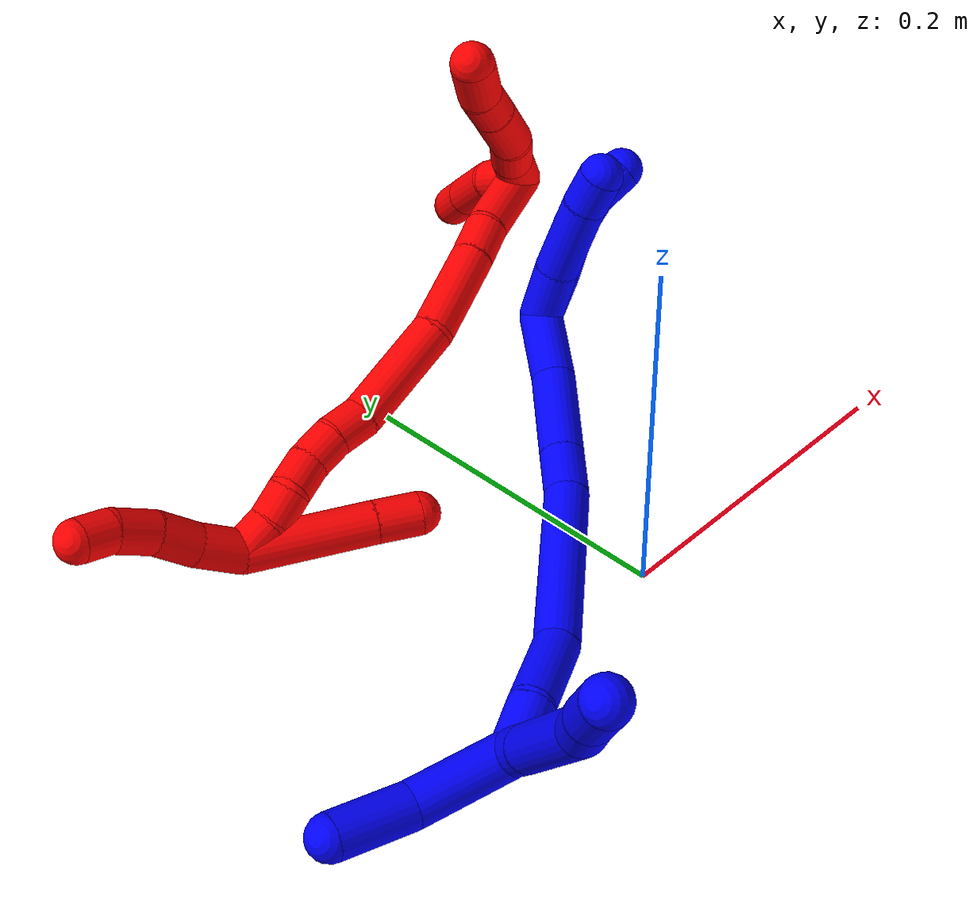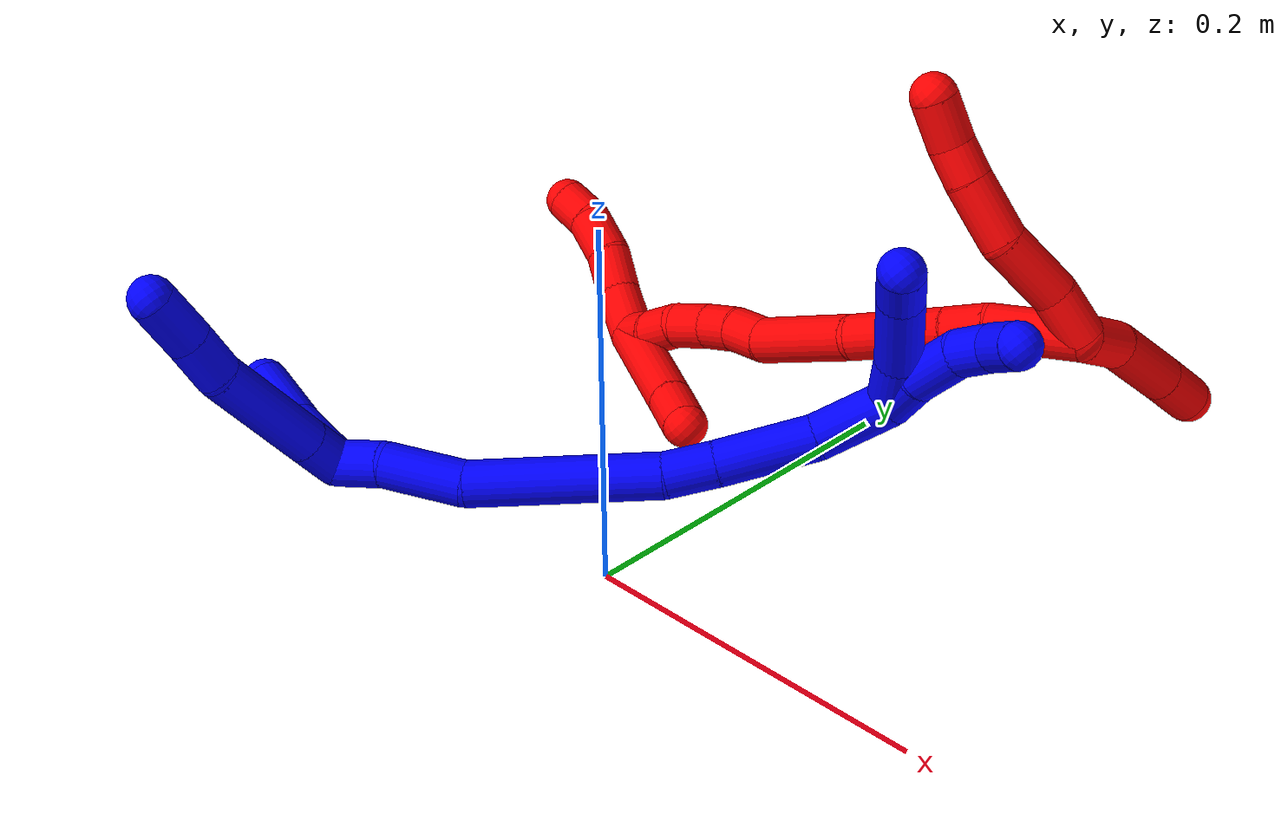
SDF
<sdf version="1.7">
 <world name="default">
  <plugin name="TubeGeneratorPlugin" filename="libtube_generator_plugin.so"/>
  <model name="photoneo_s_sensor">
   <static>1</static>
   <pose>0 0 2 1.57079 1.57079 3.14159</pose>
   <link name="link">
    <inertial><mass>0.1</mass></inertial>
    <sensor name="sensor" type="depth">
     <update_rate>30</update_rate>
     <camera>
      <horizontal_fov>1.22</horizontal_fov>
      <image><width>1920</width><height>1200</height><format>B8G8R8</format></image>
      <clip><near>0.1</near><far>4</far></clip>
      <depth_camera><output>points</output></depth_camera>
     </camera>
     <plugin name="camera_plugin" filename="libgazebo_ros_depth_camera.so">
      <baseline>0.2</baseline>
      <alwaysOn>1</alwaysOn>
      <updateRate>0.0</updateRate>
      <cameraName>camera_ir</cameraName>
      <imageTopicName>/camera/color/image_raw</imageTopicName>
      <cameraInfoTopicName>/camera/color/camera_info</cameraInfoTopicName>
      <depthImageTopicName>/camera/depth/image_raw</depthImageTopicName>
      <depthImageCameraInfoTopicName>/camera/depth/camera_info</depthImageCameraInfoTopicName>
      <pointCloudTopicName>/camera/depth/points</pointCloudTopicName>
      <frameName>fr_optical</frameName>
      <pointCloudCutoff>0.1</pointCloudCutoff>
      <pointCloudCutoffMax>2.0</pointCloudCutoffMax>
      <distortionK1>0</distortionK1>
      <distortionK2>0</distortionK2>
      <distortionK3>0</distortionK3>
      <distortionT1>0</distortionT1>
      <distortionT2>0</distortionT2>
      <CxPrime>0</CxPrime>
      <Cx>0</Cx>
      <Cy>0</Cy>
      <focalLength>0</focalLength>
      <hackBaseline>0</hackBaseline>
     </plugin>
    </sensor>
   </link>
  </model>
  <gravity>0 0 -9.8</gravity>
  <magnetic_field>6e-06 2.3e-05 -4.2e-05</magnetic_field>
  <atmosphere type="adiabatic"/>
  <physics name="default_physics" default="0" type="ode">
   <max_step_size>0.003</max_step_size>
   <real_time_factor>1</real_time_factor>
   <real_time_update_rate>1000</real_time_update_rate>
   <max_contacts>10000</max_contacts>
   <ode>
    <solver>
     <type>quick</type>
     <iters>100</iters>
     <sor>1.3</sor>
     <use_dynamic_moi_rescaling>0</use_dynamic_moi_rescaling>
    </solver>
    <constraints>
     <contact_max_correcting_vel>0</contact_max_correcting_vel>
     <contact_surface_layer>0.001</contact_surface_layer>
     <cfm>0</cfm>
     <erp>0.2</erp>
    </constraints>
   </ode>
  </physics>
  <scene><ambient>0.4 0.4 0.4 1</ambient><background>0.7 0.7 0.7 1</background><shadows>0</shadows></scene>
  <audio><device>default</device></audio>
  <spherical_coordinates>
   <surface_model>EARTH_WGS84</surface_model>
   <latitude_deg>0</latitude_deg>
   <longitude_deg>0</longitude_deg>
   <elevation>0</elevation>
   <heading_deg>0</heading_deg>
  </spherical_coordinates>
  <model name="bin">
   <static>1</static>
   <link name="bottom">
    <collision name="collision-bottom">
     <pose>0 0 -0.01 0 -0 0</pose>
     <geometry><box><size>0.8 0.6 0.02</size></box></geometry>
     <surface>
      <friction><ode><mu>100</mu><mu2>100</mu2></ode></friction>
      <contact><collide_bitmask>65535</collide_bitmask></contact>
     </surface>
    </collision>
   </link>
   <link name="west_wall">
    <collision name="collision-west_wall">
     <pose>-0.41 0 0.1 0 -0 0</pose>
     <geometry><box><size>0.02 0.6 0.2</size></box></geometry>
     <surface>
      <friction><ode><mu>100</mu><mu2>100</mu2></ode></friction>
      <contact><collide_bitmask>65535</collide_bitmask></contact>
     </surface>
    </collision>
   </link>
   <link name="east_wall">
    <collision name="collision-east_wall">
     <pose>0.41 0 0.1 0 -0 0</pose>
     <geometry><box><size>0.02 0.6 0.2</size></box></geometry>
     <surface>
      <friction><ode><mu>100</mu><mu2>100</mu2></ode></friction>
      <contact><collide_bitmask>65535</collide_bitmask></contact>
     </surface>
    </collision>
   </link>
   <link name="south_wall">
    <collision name="collision-south_wall">
     <pose>0 -0.31 0.1 0 -0 0</pose>
     <geometry><box><size>0.8 0.02 0.2</size></box></geometry>
     <surface>
      <friction><ode><mu>100</mu><mu2>100</mu2></ode></friction>
      <contact><collide_bitmask>65535</collide_bitmask></contact>
     </surface>
    </collision>
   </link>
   <link name="north_wall">
    <collision name="collision-north_wall">
     <pose>0 0.31 0.1 0 -0 0</pose>
     <geometry><box><size>0.8 0.02 0.2</size></box></geometry>
     <surface>
      <friction><ode><mu>100</mu><mu2>100</mu2></ode></friction>
      <contact><collide_bitmask>65535</collide_bitmask></contact>
     </surface>
    </collision>
   </link>
  </model>
  <model name="1">
   <static>0</static>
   <link name="1">
    <collision name="collision-cylinder-e_1_2_8">
     <pose>0.007135 -0.005083 0.008221 0.553734 0.635879 0.186497</pose>
     <geometry><cylinder><radius>0.0125</radius><length>0.024027</length></cylinder></geometry>
     <surface>
      <friction><ode><mu>1.16</mu><mu2>1.16</mu2><slip1>0</slip1><slip2>0</slip2></ode></friction>
      <contact><ode><kp>1e+06</kp><kd>1</kd><max_vel>0</max_vel><min_depth>0.001</min_depth></ode></contact>
     </surface>
    </collision>
    <visual name="visual-cylinder-e_1_2_8">
     <pose>0.007135 -0.005083 0.008221 0.553734 0.635879 0.186497</pose>
     <geometry><cylinder><radius>0.0125</radius><length>0.024027</length></cylinder></geometry>
     <material><ambient>0 0 1 1</ambient></material>
    </visual>
    <collision name="collision-cylinder-e_2_8_9">
     <pose>0.036348 -0.024799 0.038936 0.576765 0.688472 0.211909</pose>
     <geometry><cylinder><radius>0.0125</radius><length>0.069501</length></cylinder></geometry>
     <surface>
      <friction><ode><mu>1.16</mu><mu2>1.16</mu2><slip1>0</slip1><slip2>0</slip2></ode></friction>
      <contact><ode><kp>1e+06</kp><kd>1</kd><max_vel>0</max_vel><min_depth>0.001</min_depth></ode></contact>
     </surface>
    </collision>
    <visual name="visual-cylinder-e_2_8_9">
     <pose>0.036348 -0.024799 0.038936 0.576765 0.688472 0.211909</pose>
     <geometry><cylinder><radius>0.0125</radius><length>0.069501</length></cylinder></geometry>
     <material><ambient>0 0 1 1</ambient></material>
    </visual>
    <collision name="collision-cylinder-e_3_9_10">
     <pose>0.065924 -0.042315 0.071468 0.279586 0.622574 0.090485</pose>
     <geometry><cylinder><radius>0.0125</radius><length>0.025711</length></cylinder></geometry>
     <surface>
      <friction><ode><mu>1.16</mu><mu2>1.16</mu2><slip1>0</slip1><slip2>0</slip2></ode></friction>
      <contact><ode><kp>1e+06</kp><kd>1</kd><max_vel>0</max_vel><min_depth>0.001</min_depth></ode></contact>
     </surface>
    </collision>
    <visual name="visual-cylinder-e_3_9_10">
     <pose>0.065924 -0.042315 0.071468 0.279586 0.622574 0.090485</pose>
     <geometry><cylinder><radius>0.0125</radius><length>0.025711</length></cylinder></geometry>
     <material><ambient>0 0 1 1</ambient></material>
    </visual>
    <collision name="collision-cylinder-e_4_10_6">
     <pose>0.08294 -0.049301 0.092868 0.346631 0.667394 0.121232</pose>
     <geometry><cylinder><radius>0.0125</radius><length>0.030761</length></cylinder></geometry>
     <surface>
      <friction><ode><mu>1.16</mu><mu2>1.16</mu2><slip1>0</slip1><slip2>0</slip2></ode></friction>
      <contact><ode><kp>1e+06</kp><kd>1</kd><max_vel>0</max_vel><min_depth>0.001</min_depth></ode></contact>
     </surface>
    </collision>
    <visual name="visual-cylinder-e_4_10_6">
     <pose>0.08294 -0.049301 0.092868 0.346631 0.667394 0.121232</pose>
     <geometry><cylinder><radius>0.0125</radius><length>0.030761</length></cylinder></geometry>
     <material><ambient>0 0 1 1</ambient></material>
    </visual>
    <collision name="collision-cylinder-e_1_2_11">
     <pose>-0.021443 0.004589 0.017814 -0.252116 -0.861741 0.116378</pose>
     <geometry><cylinder><radius>0.0125</radius><length>0.056505</length></cylinder></geometry>
     <surface>
      <friction><ode><mu>1.16</mu><mu2>1.16</mu2><slip1>0</slip1><slip2>0</slip2></ode></friction>
      <contact><ode><kp>1e+06</kp><kd>1</kd><max_vel>0</max_vel><min_depth>0.001</min_depth></ode></contact>
     </surface>
    </collision>
    <visual name="visual-cylinder-e_1_2_11">
     <pose>-0.021443 0.004589 0.017814 -0.252116 -0.861741 0.116378</pose>
     <geometry><cylinder><radius>0.0125</radius><length>0.056505</length></cylinder></geometry>
     <material><ambient>0 0 1 1</ambient></material>
    </visual>
    <collision name="collision-cylinder-e_2_11_5">
     <pose>-0.055243 0.012792 0.053156 -0.203359 -0.604288 0.063582</pose>
     <geometry><cylinder><radius>0.0125</radius><length>0.043495</length></cylinder></geometry>
     <surface>
      <friction><ode><mu>1.16</mu><mu2>1.16</mu2><slip1>0</slip1><slip2>0</slip2></ode></friction>
      <contact><ode><kp>1e+06</kp><kd>1</kd><max_vel>0</max_vel><min_depth>0.001</min_depth></ode></contact>
     </surface>
    </collision>
    <visual name="visual-cylinder-e_2_11_5">
     <pose>-0.055243 0.012792 0.053156 -0.203359 -0.604288 0.063582</pose>
     <geometry><cylinder><radius>0.0125</radius><length>0.043495</length></cylinder></geometry>
     <material><ambient>0 0 1 1</ambient></material>
    </visual>
    <collision name="collision-cylinder-e_1_2_12">
     <pose>0.008362 0.007542 -0.008816 -2.43394 0.624501 -1.43647</pose>
     <geometry><cylinder><radius>0.0125</radius><length>0.028603</length></cylinder></geometry>
     <surface>
      <friction><ode><mu>1.16</mu><mu2>1.16</mu2><slip1>0</slip1><slip2>0</slip2></ode></friction>
      <contact><ode><kp>1e+06</kp><kd>1</kd><max_vel>0</max_vel><min_depth>0.001</min_depth></ode></contact>
     </surface>
    </collision>
    <visual name="visual-cylinder-e_1_2_12">
     <pose>0.008362 0.007542 -0.008816 -2.43394 0.624501 -1.43647</pose>
     <geometry><cylinder><radius>0.0125</radius><length>0.028603</length></cylinder></geometry>
     <material><ambient>0 0 1 1</ambient></material>
    </visual>
    <collision name="collision-cylinder-e_2_12_13">
     <pose>0.02546 0.026626 -0.035086 -2.5573 0.395491 -1.17538</pose>
     <geometry><cylinder><radius>0.0125</radius><length>0.04535</length></cylinder></geometry>
     <surface>
      <friction><ode><mu>1.16</mu><mu2>1.16</mu2><slip1>0</slip1><slip2>0</slip2></ode></friction>
      <contact><ode><kp>1e+06</kp><kd>1</kd><max_vel>0</max_vel><min_depth>0.001</min_depth></ode></contact>
     </surface>
    </collision>
    <visual name="visual-cylinder-e_2_12_13">
     <pose>0.02546 0.026626 -0.035086 -2.5573 0.395491 -1.17538</pose>
     <geometry><cylinder><radius>0.0125</radius><length>0.04535</length></cylinder></geometry>
     <material><ambient>0 0 1 1</ambient></material>
    </visual>
    <collision name="collision-cylinder-e_3_13_14">
     <pose>0.054542 0.075428 -0.082638 -2.25027 0.401686 -0.805726</pose>
     <geometry><cylinder><radius>0.0125</radius><length>0.104081</length></cylinder></geometry>
     <surface>
      <friction><ode><mu>1.16</mu><mu2>1.16</mu2><slip1>0</slip1><slip2>0</slip2></ode></friction>
      <contact><ode><kp>1e+06</kp><kd>1</kd><max_vel>0</max_vel><min_depth>0.001</min_depth></ode></contact>
     </surface>
    </collision>
    <visual name="visual-cylinder-e_3_13_14">
     <pose>0.054542 0.075428 -0.082638 -2.25027 0.401686 -0.805726</pose>
     <geometry><cylinder><radius>0.0125</radius><length>0.104081</length></cylinder></geometry>
     <material><ambient>0 0 1 1</ambient></material>
    </visual>
    <collision name="collision-cylinder-e_4_14_15">
     <pose>0.080158 0.123954 -0.118562 -2.048 0.393789 -0.633365</pose>
     <geometry><cylinder><radius>0.0125</radius><length>0.027468</length></cylinder></geometry>
     <surface>
      <friction><ode><mu>1.16</mu><mu2>1.16</mu2><slip1>0</slip1><slip2>0</slip2></ode></friction>
      <contact><ode><kp>1e+06</kp><kd>1</kd><max_vel>0</max_vel><min_depth>0.001</min_depth></ode></contact>
     </surface>
    </collision>
    <visual name="visual-cylinder-e_4_14_15">
     <pose>0.080158 0.123954 -0.118562 -2.048 0.393789 -0.633365</pose>
     <geometry><cylinder><radius>0.0125</radius><length>0.027468</length></cylinder></geometry>
     <material><ambient>0 0 1 1</ambient></material>
    </visual>
    <collision name="collision-cylinder-e_5_15_16">
     <pose>0.096346 0.156903 -0.134661 -2.01329 0.427052 -0.660283</pose>
     <geometry><cylinder><radius>0.0125</radius><length>0.052724</length></cylinder></geometry>
     <surface>
      <friction><ode><mu>1.16</mu><mu2>1.16</mu2><slip1>0</slip1><slip2>0</slip2></ode></friction>
      <contact><ode><kp>1e+06</kp><kd>1</kd><max_vel>0</max_vel><min_depth>0.001</min_depth></ode></contact>
     </surface>
    </collision>
    <visual name="visual-cylinder-e_5_15_16">
     <pose>0.096346 0.156903 -0.134661 -2.01329 0.427052 -0.660283</pose>
     <geometry><cylinder><radius>0.0125</radius><length>0.052724</length></cylinder></geometry>
     <material><ambient>0 0 1 1</ambient></material>
    </visual>
    <collision name="collision-cylinder-e_6_16_1">
     <pose>0.116676 0.196656 -0.14954 -1.82028 0.4674 -0.594469</pose>
     <geometry><cylinder><radius>0.0125</radius><length>0.041775</length></cylinder></geometry>
     <surface>
      <friction><ode><mu>1.16</mu><mu2>1.16</mu2><slip1>0</slip1><slip2>0</slip2></ode></friction>
      <contact><ode><kp>1e+06</kp><kd>1</kd><max_vel>0</max_vel><min_depth>0.001</min_depth></ode></contact>
     </surface>
    </collision>
    <visual name="visual-cylinder-e_6_16_1">
     <pose>0.116676 0.196656 -0.14954 -1.82028 0.4674 -0.594469</pose>
     <geometry><cylinder><radius>0.0125</radius><length>0.041775</length></cylinder></geometry>
     <material><ambient>0 0 1 1</ambient></material>
    </visual>
    <collision name="collision-cylinder-e_1_1_17">
     <pose>0.138339 0.218651 -0.153961 -1.52425 1.26049 -1.21649</pose>
     <geometry><cylinder><radius>0.0125</radius><length>0.025732</length></cylinder></geometry>
     <surface>
      <friction><ode><mu>1.16</mu><mu2>1.16</mu2><slip1>0</slip1><slip2>0</slip2></ode></friction>
      <contact><ode><kp>1e+06</kp><kd>1</kd><max_vel>0</max_vel><min_depth>0.001</min_depth></ode></contact>
     </surface>
    </collision>
    <visual name="visual-cylinder-e_1_1_17">
     <pose>0.138339 0.218651 -0.153961 -1.52425 1.26049 -1.21649</pose>
     <geometry><cylinder><radius>0.0125</radius><length>0.025732</length></cylinder></geometry>
     <material><ambient>0 0 1 1</ambient></material>
    </visual>
    <collision name="collision-cylinder-e_2_17_18">
     <pose>0.164269 0.22928 -0.155704 -1.85044 1.09918 -1.36547</pose>
     <geometry><cylinder><radius>0.0125</radius><length>0.030709</length></cylinder></geometry>
     <surface>
      <friction><ode><mu>1.16</mu><mu2>1.16</mu2><slip1>0</slip1><slip2>0</slip2></ode></friction>
      <contact><ode><kp>1e+06</kp><kd>1</kd><max_vel>0</max_vel><min_depth>0.001</min_depth></ode></contact>
     </surface>
    </collision>
    <visual name="visual-cylinder-e_2_17_18">
     <pose>0.164269 0.22928 -0.155704 -1.85044 1.09918 -1.36547</pose>
     <geometry><cylinder><radius>0.0125</radius><length>0.030709</length></cylinder></geometry>
     <material><ambient>0 0 1 1</ambient></material>
    </visual>
    <collision name="collision-cylinder-e_3_18_19">
     <pose>0.187248 0.23943 -0.161995 -2.47355 1.03189 -2.04345</pose>
     <geometry><cylinder><radius>0.0125</radius><length>0.021674</length></cylinder></geometry>
     <surface>
      <friction><ode><mu>1.16</mu><mu2>1.16</mu2><slip1>0</slip1><slip2>0</slip2></ode></friction>
      <contact><ode><kp>1e+06</kp><kd>1</kd><max_vel>0</max_vel><min_depth>0.001</min_depth></ode></contact>
     </surface>
    </collision>
    <visual name="visual-cylinder-e_3_18_19">
     <pose>0.187248 0.23943 -0.161995 -2.47355 1.03189 -2.04345</pose>
     <geometry><cylinder><radius>0.0125</radius><length>0.021674</length></cylinder></geometry>
     <material><ambient>0 0 1 1</ambient></material>
    </visual>
    <collision name="collision-cylinder-e_4_19_4">
     <pose>0.206811 0.242945 -0.170159 -3.1233 1.2163 -3.11531</pose>
     <geometry><cylinder><radius>0.0125</radius><length>0.021884</length></cylinder></geometry>
     <surface>
      <friction><ode><mu>1.16</mu><mu2>1.16</mu2><slip1>0</slip1><slip2>0</slip2></ode></friction>
      <contact><ode><kp>1e+06</kp><kd>1</kd><max_vel>0</max_vel><min_depth>0.001</min_depth></ode></contact>
     </surface>
    </collision>
    <visual name="visual-cylinder-e_4_19_4">
     <pose>0.206811 0.242945 -0.170159 -3.1233 1.2163 -3.11531</pose>
     <geometry><cylinder><radius>0.0125</radius><length>0.021884</length></cylinder></geometry>
     <material><ambient>0 0 1 1</ambient></material>
    </visual>
    <collision name="collision-cylinder-e_1_1_20">
     <pose>0.140732 0.21675 -0.147534 -0.297138 1.1298 -0.189158</pose>
     <geometry><cylinder><radius>0.0125</radius><length>0.032388</length></cylinder></geometry>
     <surface>
      <friction><ode><mu>1.16</mu><mu2>1.16</mu2><slip1>0</slip1><slip2>0</slip2></ode></friction>
      <contact><ode><kp>1e+06</kp><kd>1</kd><max_vel>0</max_vel><min_depth>0.001</min_depth></ode></contact>
     </surface>
    </collision>
    <visual name="visual-cylinder-e_1_1_20">
     <pose>0.140732 0.21675 -0.147534 -0.297138 1.1298 -0.189158</pose>
     <geometry><cylinder><radius>0.0125</radius><length>0.032388</length></cylinder></geometry>
     <material><ambient>0 0 1 1</ambient></material>
    </visual>
    <collision name="collision-cylinder-e_2_20_21">
     <pose>0.176013 0.218911 -0.130691 -0.013401 1.11038 -0.008312</pose>
     <geometry><cylinder><radius>0.0125</radius><length>0.046072</length></cylinder></geometry>
     <surface>
      <friction><ode><mu>1.16</mu><mu2>1.16</mu2><slip1>0</slip1><slip2>0</slip2></ode></friction>
      <contact><ode><kp>1e+06</kp><kd>1</kd><max_vel>0</max_vel><min_depth>0.001</min_depth></ode></contact>
     </surface>
    </collision>
    <visual name="visual-cylinder-e_2_20_21">
     <pose>0.176013 0.218911 -0.130691 -0.013401 1.11038 -0.008312</pose>
     <geometry><cylinder><radius>0.0125</radius><length>0.046072</length></cylinder></geometry>
     <material><ambient>0 0 1 1</ambient></material>
    </visual>
    <collision name="collision-cylinder-e_3_21_3">
     <pose>0.206527 0.218397 -0.116211 0.152204 1.16058 0.099892</pose>
     <geometry><cylinder><radius>0.0125</radius><length>0.02154</length></cylinder></geometry>
     <surface>
      <friction><ode><mu>1.16</mu><mu2>1.16</mu2><slip1>0</slip1><slip2>0</slip2></ode></friction>
      <contact><ode><kp>1e+06</kp><kd>1</kd><max_vel>0</max_vel><min_depth>0.001</min_depth></ode></contact>
     </surface>
    </collision>
    <visual name="visual-cylinder-e_3_21_3">
     <pose>0.206527 0.218397 -0.116211 0.152204 1.16058 0.099892</pose>
     <geometry><cylinder><radius>0.0125</radius><length>0.02154</length></cylinder></geometry>
     <material><ambient>0 0 1 1</ambient></material>
    </visual>
    <collision name="collision-sphere-3">
     <pose>0.216404 0.217746 -0.111965 0 -0 0</pose>
     <geometry><sphere><radius>0.0125</radius></sphere></geometry>
     <surface>
      <friction><ode><mu>1.16</mu><mu2>1.16</mu2><slip1>0</slip1><slip2>0</slip2></ode></friction>
      <contact><ode><kp>1e+06</kp><kd>1</kd><max_vel>0</max_vel><min_depth>0.001</min_depth></ode></contact>
     </surface>
    </collision>
    <visual name="visual-sphere-3">
     <pose>0.216404 0.217746 -0.111965 0 -0 0</pose>
     <geometry><sphere><radius>0.0125</radius></sphere></geometry>
     <material><ambient>0 0 1 1</ambient></material>
    </visual>
    <collision name="collision-sphere-21">
     <pose>0.196651 0.219048 -0.120456 0 -0 0</pose>
     <geometry><sphere><radius>0.0125</radius></sphere></geometry>
     <surface>
      <friction><ode><mu>1.16</mu><mu2>1.16</mu2><slip1>0</slip1><slip2>0</slip2></ode></friction>
      <contact><ode><kp>1e+06</kp><kd>1</kd><max_vel>0</max_vel><min_depth>0.001</min_depth></ode></contact>
     </surface>
    </collision>
    <visual name="visual-sphere-21">
     <pose>0.196651 0.219048 -0.120456 0 -0 0</pose>
     <geometry><sphere><radius>0.0125</radius></sphere></geometry>
     <material><ambient>0 0 1 1</ambient></material>
    </visual>
    <collision name="collision-sphere-20">
     <pose>0.155376 0.218774 -0.140925 0 -0 0</pose>
     <geometry><sphere><radius>0.0125</radius></sphere></geometry>
     <surface>
      <friction><ode><mu>1.16</mu><mu2>1.16</mu2><slip1>0</slip1><slip2>0</slip2></ode></friction>
      <contact><ode><kp>1e+06</kp><kd>1</kd><max_vel>0</max_vel><min_depth>0.001</min_depth></ode></contact>
     </surface>
    </collision>
    <visual name="visual-sphere-20">
     <pose>0.155376 0.218774 -0.140925 0 -0 0</pose>
     <geometry><sphere><radius>0.0125</radius></sphere></geometry>
     <material><ambient>0 0 1 1</ambient></material>
    </visual>
    <collision name="collision-sphere-4">
     <pose>0.217073 0.243014 -0.173956 0 -0 0</pose>
     <geometry><sphere><radius>0.0125</radius></sphere></geometry>
     <surface>
      <friction><ode><mu>1.16</mu><mu2>1.16</mu2><slip1>0</slip1><slip2>0</slip2></ode></friction>
      <contact><ode><kp>1e+06</kp><kd>1</kd><max_vel>0</max_vel><min_depth>0.001</min_depth></ode></contact>
     </surface>
    </collision>
    <visual name="visual-sphere-4">
     <pose>0.217073 0.243014 -0.173956 0 -0 0</pose>
     <geometry><sphere><radius>0.0125</radius></sphere></geometry>
     <material><ambient>0 0 1 1</ambient></material>
    </visual>
    <collision name="collision-sphere-11">
     <pose>-0.042886 0.009178 0.035629 0 -0 0</pose>
     <geometry><sphere><radius>0.0125</radius></sphere></geometry>
     <surface>
      <friction><ode><mu>1.16</mu><mu2>1.16</mu2><slip1>0</slip1><slip2>0</slip2></ode></friction>
      <contact><ode><kp>1e+06</kp><kd>1</kd><max_vel>0</max_vel><min_depth>0.001</min_depth></ode></contact>
     </surface>
    </collision>
    <visual name="visual-sphere-11">
     <pose>-0.042886 0.009178 0.035629 0 -0 0</pose>
     <geometry><sphere><radius>0.0125</radius></sphere></geometry>
     <material><ambient>0 0 1 1</ambient></material>
    </visual>
    <collision name="collision-sphere-6">
     <pose>0.092459 -0.053405 0.10423 0 -0 0</pose>
     <geometry><sphere><radius>0.0125</radius></sphere></geometry>
     <surface>
      <friction><ode><mu>1.16</mu><mu2>1.16</mu2><slip1>0</slip1><slip2>0</slip2></ode></friction>
      <contact><ode><kp>1e+06</kp><kd>1</kd><max_vel>0</max_vel><min_depth>0.001</min_depth></ode></contact>
     </surface>
    </collision>
    <visual name="visual-sphere-6">
     <pose>0.092459 -0.053405 0.10423 0 -0 0</pose>
     <geometry><sphere><radius>0.0125</radius></sphere></geometry>
     <material><ambient>0 0 1 1</ambient></material>
    </visual>
    <collision name="collision-sphere-10">
     <pose>0.07342 -0.045197 0.081506 0 -0 0</pose>
     <geometry><sphere><radius>0.0125</radius></sphere></geometry>
     <surface>
      <friction><ode><mu>1.16</mu><mu2>1.16</mu2><slip1>0</slip1><slip2>0</slip2></ode></friction>
      <contact><ode><kp>1e+06</kp><kd>1</kd><max_vel>0</max_vel><min_depth>0.001</min_depth></ode></contact>
     </surface>
    </collision>
    <visual name="visual-sphere-10">
     <pose>0.07342 -0.045197 0.081506 0 -0 0</pose>
     <geometry><sphere><radius>0.0125</radius></sphere></geometry>
     <material><ambient>0 0 1 1</ambient></material>
    </visual>
    <collision name="collision-sphere-9">
     <pose>0.058428 -0.039433 0.06143 0 -0 0</pose>
     <geometry><sphere><radius>0.0125</radius></sphere></geometry>
     <surface>
      <friction><ode><mu>1.16</mu><mu2>1.16</mu2><slip1>0</slip1><slip2>0</slip2></ode></friction>
      <contact><ode><kp>1e+06</kp><kd>1</kd><max_vel>0</max_vel><min_depth>0.001</min_depth></ode></contact>
     </surface>
    </collision>
    <visual name="visual-sphere-9">
     <pose>0.058428 -0.039433 0.06143 0 -0 0</pose>
     <geometry><sphere><radius>0.0125</radius></sphere></geometry>
     <material><ambient>0 0 1 1</ambient></material>
    </visual>
    <collision name="collision-sphere-2">
     <geometry><sphere><radius>0.0125</radius></sphere></geometry>
     <surface>
      <friction><ode><mu>1.16</mu><mu2>1.16</mu2><slip1>0</slip1><slip2>0</slip2></ode></friction>
      <contact><ode><kp>1e+06</kp><kd>1</kd><max_vel>0</max_vel><min_depth>0.001</min_depth></ode></contact>
     </surface>
    </collision>
    <visual name="visual-sphere-2">
     <geometry><sphere><radius>0.0125</radius></sphere></geometry>
     <material><ambient>0 0 1 1</ambient></material>
    </visual>
    <collision name="collision-sphere-19">
     <pose>0.19655 0.242875 -0.166361 0 -0 0</pose>
     <geometry><sphere><radius>0.0125</radius></sphere></geometry>
     <surface>
      <friction><ode><mu>1.16</mu><mu2>1.16</mu2><slip1>0</slip1><slip2>0</slip2></ode></friction>
      <contact><ode><kp>1e+06</kp><kd>1</kd><max_vel>0</max_vel><min_depth>0.001</min_depth></ode></contact>
     </surface>
    </collision>
    <visual name="visual-sphere-19">
     <pose>0.19655 0.242875 -0.166361 0 -0 0</pose>
     <geometry><sphere><radius>0.0125</radius></sphere></geometry>
     <material><ambient>0 0 1 1</ambient></material>
    </visual>
    <collision name="collision-sphere-8">
     <pose>0.014269 -0.010165 0.016442 0 -0 0</pose>
     <geometry><sphere><radius>0.0125</radius></sphere></geometry>
     <surface>
      <friction><ode><mu>1.16</mu><mu2>1.16</mu2><slip1>0</slip1><slip2>0</slip2></ode></friction>
      <contact><ode><kp>1e+06</kp><kd>1</kd><max_vel>0</max_vel><min_depth>0.001</min_depth></ode></contact>
     </surface>
    </collision>
    <visual name="visual-sphere-8">
     <pose>0.014269 -0.010165 0.016442 0 -0 0</pose>
     <geometry><sphere><radius>0.0125</radius></sphere></geometry>
     <material><ambient>0 0 1 1</ambient></material>
    </visual>
    <collision name="collision-sphere-5">
     <pose>-0.067599 0.016406 0.070683 0 -0 0</pose>
     <geometry><sphere><radius>0.0125</radius></sphere></geometry>
     <surface>
      <friction><ode><mu>1.16</mu><mu2>1.16</mu2><slip1>0</slip1><slip2>0</slip2></ode></friction>
      <contact><ode><kp>1e+06</kp><kd>1</kd><max_vel>0</max_vel><min_depth>0.001</min_depth></ode></contact>
     </surface>
    </collision>
    <visual name="visual-sphere-5">
     <pose>-0.067599 0.016406 0.070683 0 -0 0</pose>
     <geometry><sphere><radius>0.0125</radius></sphere></geometry>
     <material><ambient>0 0 1 1</ambient></material>
    </visual>
    <collision name="collision-sphere-12">
     <pose>0.016724 0.015084 -0.017633 0 -0 0</pose>
     <geometry><sphere><radius>0.0125</radius></sphere></geometry>
     <surface>
      <friction><ode><mu>1.16</mu><mu2>1.16</mu2><slip1>0</slip1><slip2>0</slip2></ode></friction>
      <contact><ode><kp>1e+06</kp><kd>1</kd><max_vel>0</max_vel><min_depth>0.001</min_depth></ode></contact>
     </surface>
    </collision>
    <visual name="visual-sphere-12">
     <pose>0.016724 0.015084 -0.017633 0 -0 0</pose>
     <geometry><sphere><radius>0.0125</radius></sphere></geometry>
     <material><ambient>0 0 1 1</ambient></material>
    </visual>
    <collision name="collision-sphere-13">
     <pose>0.034196 0.038168 -0.052539 0 -0 0</pose>
     <geometry><sphere><radius>0.0125</radius></sphere></geometry>
     <surface>
      <friction><ode><mu>1.16</mu><mu2>1.16</mu2><slip1>0</slip1><slip2>0</slip2></ode></friction>
      <contact><ode><kp>1e+06</kp><kd>1</kd><max_vel>0</max_vel><min_depth>0.001</min_depth></ode></contact>
     </surface>
    </collision>
    <visual name="visual-sphere-13">
     <pose>0.034196 0.038168 -0.052539 0 -0 0</pose>
     <geometry><sphere><radius>0.0125</radius></sphere></geometry>
     <material><ambient>0 0 1 1</ambient></material>
    </visual>
    <collision name="collision-sphere-14">
     <pose>0.074888 0.112688 -0.112737 0 -0 0</pose>
     <geometry><sphere><radius>0.0125</radius></sphere></geometry>
     <surface>
      <friction><ode><mu>1.16</mu><mu2>1.16</mu2><slip1>0</slip1><slip2>0</slip2></ode></friction>
      <contact><ode><kp>1e+06</kp><kd>1</kd><max_vel>0</max_vel><min_depth>0.001</min_depth></ode></contact>
     </surface>
    </collision>
    <visual name="visual-sphere-14">
     <pose>0.074888 0.112688 -0.112737 0 -0 0</pose>
     <geometry><sphere><radius>0.0125</radius></sphere></geometry>
     <material><ambient>0 0 1 1</ambient></material>
    </visual>
    <collision name="collision-sphere-15">
     <pose>0.085427 0.13522 -0.124387 0 -0 0</pose>
     <geometry><sphere><radius>0.0125</radius></sphere></geometry>
     <surface>
      <friction><ode><mu>1.16</mu><mu2>1.16</mu2><slip1>0</slip1><slip2>0</slip2></ode></friction>
      <contact><ode><kp>1e+06</kp><kd>1</kd><max_vel>0</max_vel><min_depth>0.001</min_depth></ode></contact>
     </surface>
    </collision>
    <visual name="visual-sphere-15">
     <pose>0.085427 0.13522 -0.124387 0 -0 0</pose>
     <geometry><sphere><radius>0.0125</radius></sphere></geometry>
     <material><ambient>0 0 1 1</ambient></material>
    </visual>
    <collision name="collision-sphere-16">
     <pose>0.107265 0.178587 -0.144936 0 -0 0</pose>
     <geometry><sphere><radius>0.0125</radius></sphere></geometry>
     <surface>
      <friction><ode><mu>1.16</mu><mu2>1.16</mu2><slip1>0</slip1><slip2>0</slip2></ode></friction>
      <contact><ode><kp>1e+06</kp><kd>1</kd><max_vel>0</max_vel><min_depth>0.001</min_depth></ode></contact>
     </surface>
    </collision>
    <visual name="visual-sphere-16">
     <pose>0.107265 0.178587 -0.144936 0 -0 0</pose>
     <geometry><sphere><radius>0.0125</radius></sphere></geometry>
     <material><ambient>0 0 1 1</ambient></material>
    </visual>
    <collision name="collision-sphere-1">
     <pose>0.126087 0.214726 -0.154144 0 -0 0</pose>
     <geometry><sphere><radius>0.0125</radius></sphere></geometry>
     <surface>
      <friction><ode><mu>1.16</mu><mu2>1.16</mu2><slip1>0</slip1><slip2>0</slip2></ode></friction>
      <contact><ode><kp>1e+06</kp><kd>1</kd><max_vel>0</max_vel><min_depth>0.001</min_depth></ode></contact>
     </surface>
    </collision>
    <visual name="visual-sphere-1">
     <pose>0.126087 0.214726 -0.154144 0 -0 0</pose>
     <geometry><sphere><radius>0.0125</radius></sphere></geometry>
     <material><ambient>0 0 1 1</ambient></material>
    </visual>
    <collision name="collision-sphere-18">
     <pose>0.177947 0.235985 -0.157629 0 -0 0</pose>
     <geometry><sphere><radius>0.0125</radius></sphere></geometry>
     <surface>
      <friction><ode><mu>1.16</mu><mu2>1.16</mu2><slip1>0</slip1><slip2>0</slip2></ode></friction>
      <contact><ode><kp>1e+06</kp><kd>1</kd><max_vel>0</max_vel><min_depth>0.001</min_depth></ode></contact>
     </surface>
    </collision>
    <visual name="visual-sphere-18">
     <pose>0.177947 0.235985 -0.157629 0 -0 0</pose>
     <geometry><sphere><radius>0.0125</radius></sphere></geometry>
     <material><ambient>0 0 1 1</ambient></material>
    </visual>
    <collision name="collision-sphere-17">
     <pose>0.15059 0.222575 -0.153778 0 -0 0</pose>
     <geometry><sphere><radius>0.0125</radius></sphere></geometry>
     <surface>
      <friction><ode><mu>1.16</mu><mu2>1.16</mu2><slip1>0</slip1><slip2>0</slip2></ode></friction>
      <contact><ode><kp>1e+06</kp><kd>1</kd><max_vel>0</max_vel><min_depth>0.001</min_depth></ode></contact>
     </surface>
    </collision>
    <visual name="visual-sphere-17">
     <pose>0.15059 0.222575 -0.153778 0 -0 0</pose>
     <geometry><sphere><radius>0.0125</radius></sphere></geometry>
     <material><ambient>0 0 1 1</ambient></material>
    </visual>
    <inertial>
     <pose>0.075814 0.094021 -0.06055 0 -0 0</pose>
     <mass>0.75</mass>
     <inertia><ixx>8e-05</ixx><ixy>0</ixy><ixz>0</ixz><iyy>-7e-06</iyy><iyz>0</iyz><izz>-0.00017</izz></inertia>
    </inertial>
   </link>
   <pose>-0.154092 -0.046555 0.020266 0.369511 -0.847114 -0.394528</pose>
  </model>
  <model name="2">
   <static>0</static>
   <link name="2">
    <collision name="collision-cylinder-e_1_2_8">
     <pose>0.002032 -0.00251 -0.013766 2.96122 0.144218 1.34796</pose>
     <geometry><cylinder><radius>0.0125</radius><length>0.028279</length></cylinder></geometry>
     <surface>
      <friction><ode><mu>1.16</mu><mu2>1.16</mu2><slip1>0</slip1><slip2>0</slip2></ode></friction>
      <contact><ode><kp>1e+06</kp><kd>1</kd><max_vel>0</max_vel><min_depth>0.001</min_depth></ode></contact>
     </surface>
    </collision>
    <visual name="visual-cylinder-e_1_2_8">
     <pose>0.002032 -0.00251 -0.013766 2.96122 0.144218 1.34796</pose>
     <geometry><cylinder><radius>0.0125</radius><length>0.028279</length></cylinder></geometry>
     <material><ambient>1 0 0 1</ambient></material>
    </visual>
    <collision name="collision-cylinder-e_2_8_9">
     <pose>0.008774 -0.004752 -0.04711 -3.12786 0.236068 -3.02596</pose>
     <geometry><cylinder><radius>0.0125</radius><length>0.040278</length></cylinder></geometry>
     <surface>
      <friction><ode><mu>1.16</mu><mu2>1.16</mu2><slip1>0</slip1><slip2>0</slip2></ode></friction>
      <contact><ode><kp>1e+06</kp><kd>1</kd><max_vel>0</max_vel><min_depth>0.001</min_depth></ode></contact>
     </surface>
    </collision>
    <visual name="visual-cylinder-e_2_8_9">
     <pose>0.008774 -0.004752 -0.04711 -3.12786 0.236068 -3.02596</pose>
     <geometry><cylinder><radius>0.0125</radius><length>0.040278</length></cylinder></geometry>
     <material><ambient>1 0 0 1</ambient></material>
    </visual>
    <collision name="collision-cylinder-e_3_9_10">
     <pose>0.014202 -0.00874 -0.083916 2.89933 0.040424 0.329122</pose>
     <geometry><cylinder><radius>0.0125</radius><length>0.035521</length></cylinder></geometry>
     <surface>
      <friction><ode><mu>1.16</mu><mu2>1.16</mu2><slip1>0</slip1><slip2>0</slip2></ode></friction>
      <contact><ode><kp>1e+06</kp><kd>1</kd><max_vel>0</max_vel><min_depth>0.001</min_depth></ode></contact>
     </surface>
    </collision>
    <visual name="visual-cylinder-e_3_9_10">
     <pose>0.014202 -0.00874 -0.083916 2.89933 0.040424 0.329122</pose>
     <geometry><cylinder><radius>0.0125</radius><length>0.035521</length></cylinder></geometry>
     <material><ambient>1 0 0 1</ambient></material>
    </visual>
    <collision name="collision-cylinder-e_4_10_11">
     <pose>0.014942 -0.016147 -0.11065 2.82172 0.00223 0.013823</pose>
     <geometry><cylinder><radius>0.0125</radius><length>0.020029</length></cylinder></geometry>
     <surface>
      <friction><ode><mu>1.16</mu><mu2>1.16</mu2><slip1>0</slip1><slip2>0</slip2></ode></friction>
      <contact><ode><kp>1e+06</kp><kd>1</kd><max_vel>0</max_vel><min_depth>0.001</min_depth></ode></contact>
     </surface>
    </collision>
    <visual name="visual-cylinder-e_4_10_11">
     <pose>0.014942 -0.016147 -0.11065 2.82172 0.00223 0.013823</pose>
     <geometry><cylinder><radius>0.0125</radius><length>0.020029</length></cylinder></geometry>
     <material><ambient>1 0 0 1</ambient></material>
    </visual>
    <collision name="collision-cylinder-e_5_11_6">
     <pose>0.017783 -0.024085 -0.13185 2.75289 0.219469 1.02059</pose>
     <geometry><cylinder><radius>0.0125</radius><length>0.025893</length></cylinder></geometry>
     <surface>
      <friction><ode><mu>1.16</mu><mu2>1.16</mu2><slip1>0</slip1><slip2>0</slip2></ode></friction>
      <contact><ode><kp>1e+06</kp><kd>1</kd><max_vel>0</max_vel><min_depth>0.001</min_depth></ode></contact>
     </surface>
    </collision>
    <visual name="visual-cylinder-e_5_11_6">
     <pose>0.017783 -0.024085 -0.13185 2.75289 0.219469 1.02059</pose>
     <geometry><cylinder><radius>0.0125</radius><length>0.025893</length></cylinder></geometry>
     <material><ambient>1 0 0 1</ambient></material>
    </visual>
    <collision name="collision-cylinder-e_1_2_12">
     <pose>-0.010221 -0.005365 0.009618 0.508796 -0.748149 -0.203451</pose>
     <geometry><cylinder><radius>0.0125</radius><length>0.03005</length></cylinder></geometry>
     <surface>
      <friction><ode><mu>1.16</mu><mu2>1.16</mu2><slip1>0</slip1><slip2>0</slip2></ode></friction>
      <contact><ode><kp>1e+06</kp><kd>1</kd><max_vel>0</max_vel><min_depth>0.001</min_depth></ode></contact>
     </surface>
    </collision>
    <visual name="visual-cylinder-e_1_2_12">
     <pose>-0.010221 -0.005365 0.009618 0.508796 -0.748149 -0.203451</pose>
     <geometry><cylinder><radius>0.0125</radius><length>0.03005</length></cylinder></geometry>
     <material><ambient>1 0 0 1</ambient></material>
    </visual>
    <collision name="collision-cylinder-e_2_12_13">
     <pose>-0.032308 -0.013853 0.036649 0.177503 -0.590749 -0.054139</pose>
     <geometry><cylinder><radius>0.0125</radius><length>0.042605</length></cylinder></geometry>
     <surface>
      <friction><ode><mu>1.16</mu><mu2>1.16</mu2><slip1>0</slip1><slip2>0</slip2></ode></friction>
      <contact><ode><kp>1e+06</kp><kd>1</kd><max_vel>0</max_vel><min_depth>0.001</min_depth></ode></contact>
     </surface>
    </collision>
    <visual name="visual-cylinder-e_2_12_13">
     <pose>-0.032308 -0.013853 0.036649 0.177503 -0.590749 -0.054139</pose>
     <geometry><cylinder><radius>0.0125</radius><length>0.042605</length></cylinder></geometry>
     <material><ambient>1 0 0 1</ambient></material>
    </visual>
    <collision name="collision-cylinder-e_3_13_5">
     <pose>-0.051889 -0.018768 0.065208 0.159372 -0.599649 -0.049363</pose>
     <geometry><cylinder><radius>0.0125</radius><length>0.027345</length></cylinder></geometry>
     <surface>
      <friction><ode><mu>1.16</mu><mu2>1.16</mu2><slip1>0</slip1><slip2>0</slip2></ode></friction>
      <contact><ode><kp>1e+06</kp><kd>1</kd><max_vel>0</max_vel><min_depth>0.001</min_depth></ode></contact>
     </surface>
    </collision>
    <visual name="visual-cylinder-e_3_13_5">
     <pose>-0.051889 -0.018768 0.065208 0.159372 -0.599649 -0.049363</pose>
     <geometry><cylinder><radius>0.0125</radius><length>0.027345</length></cylinder></geometry>
     <material><ambient>1 0 0 1</ambient></material>
    </visual>
    <collision name="collision-cylinder-e_1_2_14">
     <pose>-0.011738 0.014598 -0.016617 -2.4208 -0.487907 1.16744</pose>
     <geometry><cylinder><radius>0.0125</radius><length>0.050081</length></cylinder></geometry>
     <surface>
      <friction><ode><mu>1.16</mu><mu2>1.16</mu2><slip1>0</slip1><slip2>0</slip2></ode></friction>
      <contact><ode><kp>1e+06</kp><kd>1</kd><max_vel>0</max_vel><min_depth>0.001</min_depth></ode></contact>
     </surface>
    </collision>
    <visual name="visual-cylinder-e_1_2_14">
     <pose>-0.011738 0.014598 -0.016617 -2.4208 -0.487907 1.16744</pose>
     <geometry><cylinder><radius>0.0125</radius><length>0.050081</length></cylinder></geometry>
     <material><ambient>1 0 0 1</ambient></material>
    </visual>
    <collision name="collision-cylinder-e_2_14_15">
     <pose>-0.029354 0.037452 -0.039175 -2.19448 -0.523966 0.964169</pose>
     <geometry><cylinder><radius>0.0125</radius><length>0.023493</length></cylinder></geometry>
     <surface>
      <friction><ode><mu>1.16</mu><mu2>1.16</mu2><slip1>0</slip1><slip2>0</slip2></ode></friction>
      <contact><ode><kp>1e+06</kp><kd>1</kd><max_vel>0</max_vel><min_depth>0.001</min_depth></ode></contact>
     </surface>
    </collision>
    <visual name="visual-cylinder-e_2_14_15">
     <pose>-0.029354 0.037452 -0.039175 -2.19448 -0.523966 0.964169</pose>
     <geometry><cylinder><radius>0.0125</radius><length>0.023493</length></cylinder></geometry>
     <material><ambient>1 0 0 1</ambient></material>
    </visual>
    <collision name="collision-cylinder-e_3_15_16">
     <pose>-0.05052 0.064524 -0.058666 -2.19495 -0.582923 1.05978</pose>
     <geometry><cylinder><radius>0.0125</radius><length>0.05555</length></cylinder></geometry>
     <surface>
      <friction><ode><mu>1.16</mu><mu2>1.16</mu2><slip1>0</slip1><slip2>0</slip2></ode></friction>
      <contact><ode><kp>1e+06</kp><kd>1</kd><max_vel>0</max_vel><min_depth>0.001</min_depth></ode></contact>
     </surface>
    </collision>
    <visual name="visual-cylinder-e_3_15_16">
     <pose>-0.05052 0.064524 -0.058666 -2.19495 -0.582923 1.05978</pose>
     <geometry><cylinder><radius>0.0125</radius><length>0.05555</length></cylinder></geometry>
     <material><ambient>1 0 0 1</ambient></material>
    </visual>
    <collision name="collision-cylinder-e_4_16_17">
     <pose>-0.090467 0.100983 -0.084453 -2.17716 -0.854396 1.43166</pose>
     <geometry><cylinder><radius>0.0125</radius><length>0.065391</length></cylinder></geometry>
     <surface>
      <friction><ode><mu>1.16</mu><mu2>1.16</mu2><slip1>0</slip1><slip2>0</slip2></ode></friction>
      <contact><ode><kp>1e+06</kp><kd>1</kd><max_vel>0</max_vel><min_depth>0.001</min_depth></ode></contact>
     </surface>
    </collision>
    <visual name="visual-cylinder-e_4_16_17">
     <pose>-0.090467 0.100983 -0.084453 -2.17716 -0.854396 1.43166</pose>
     <geometry><cylinder><radius>0.0125</radius><length>0.065391</length></cylinder></geometry>
     <material><ambient>1 0 0 1</ambient></material>
    </visual>
    <collision name="collision-cylinder-e_5_17_18">
     <pose>-0.123263 0.122218 -0.103143 -2.63368 -0.833765 2.08127</pose>
     <geometry><cylinder><radius>0.0125</radius><length>0.02198</length></cylinder></geometry>
     <surface>
      <friction><ode><mu>1.16</mu><mu2>1.16</mu2><slip1>0</slip1><slip2>0</slip2></ode></friction>
      <contact><ode><kp>1e+06</kp><kd>1</kd><max_vel>0</max_vel><min_depth>0.001</min_depth></ode></contact>
     </surface>
    </collision>
    <visual name="visual-cylinder-e_5_17_18">
     <pose>-0.123263 0.122218 -0.103143 -2.63368 -0.833765 2.08127</pose>
     <geometry><cylinder><radius>0.0125</radius><length>0.02198</length></cylinder></geometry>
     <material><ambient>1 0 0 1</ambient></material>
    </visual>
    <collision name="collision-cylinder-e_6_18_19">
     <pose>-0.138945 0.130831 -0.114617 -2.35616 -0.815663 1.61291</pose>
     <geometry><cylinder><radius>0.0125</radius><length>0.020719</length></cylinder></geometry>
     <surface>
      <friction><ode><mu>1.16</mu><mu2>1.16</mu2><slip1>0</slip1><slip2>0</slip2></ode></friction>
      <contact><ode><kp>1e+06</kp><kd>1</kd><max_vel>0</max_vel><min_depth>0.001</min_depth></ode></contact>
     </surface>
    </collision>
    <visual name="visual-cylinder-e_6_18_19">
     <pose>-0.138945 0.130831 -0.114617 -2.35616 -0.815663 1.61291</pose>
     <geometry><cylinder><radius>0.0125</radius><length>0.020719</length></cylinder></geometry>
     <material><ambient>1 0 0 1</ambient></material>
    </visual>
    <collision name="collision-cylinder-e_7_19_20">
     <pose>-0.152299 0.142328 -0.125444 -2.30173 -0.588949 1.19337</pose>
     <geometry><cylinder><radius>0.0125</radius><length>0.020921</length></cylinder></geometry>
     <surface>
      <friction><ode><mu>1.16</mu><mu2>1.16</mu2><slip1>0</slip1><slip2>0</slip2></ode></friction>
      <contact><ode><kp>1e+06</kp><kd>1</kd><max_vel>0</max_vel><min_depth>0.001</min_depth></ode></contact>
     </surface>
    </collision>
    <visual name="visual-cylinder-e_7_19_20">
     <pose>-0.152299 0.142328 -0.125444 -2.30173 -0.588949 1.19337</pose>
     <geometry><cylinder><radius>0.0125</radius><length>0.020921</length></cylinder></geometry>
     <material><ambient>1 0 0 1</ambient></material>
    </visual>
    <collision name="collision-cylinder-e_8_20_21">
     <pose>-0.165389 0.155422 -0.133992 -1.96354 -0.793457 1.1201</pose>
     <geometry><cylinder><radius>0.0125</radius><length>0.020426</length></cylinder></geometry>
     <surface>
      <friction><ode><mu>1.16</mu><mu2>1.16</mu2><slip1>0</slip1><slip2>0</slip2></ode></friction>
      <contact><ode><kp>1e+06</kp><kd>1</kd><max_vel>0</max_vel><min_depth>0.001</min_depth></ode></contact>
     </surface>
    </collision>
    <visual name="visual-cylinder-e_8_20_21">
     <pose>-0.165389 0.155422 -0.133992 -1.96354 -0.793457 1.1201</pose>
     <geometry><cylinder><radius>0.0125</radius><length>0.020426</length></cylinder></geometry>
     <material><ambient>1 0 0 1</ambient></material>
    </visual>
    <collision name="collision-cylinder-e_9_21_1">
     <pose>-0.181809 0.167071 -0.139193 -2.02545 -1.02107 1.46248</pose>
     <geometry><cylinder><radius>0.0125</radius><length>0.021438</length></cylinder></geometry>
     <surface>
      <friction><ode><mu>1.16</mu><mu2>1.16</mu2><slip1>0</slip1><slip2>0</slip2></ode></friction>
      <contact><ode><kp>1e+06</kp><kd>1</kd><max_vel>0</max_vel><min_depth>0.001</min_depth></ode></contact>
     </surface>
    </collision>
    <visual name="visual-cylinder-e_9_21_1">
     <pose>-0.181809 0.167071 -0.139193 -2.02545 -1.02107 1.46248</pose>
     <geometry><cylinder><radius>0.0125</radius><length>0.021438</length></cylinder></geometry>
     <material><ambient>1 0 0 1</ambient></material>
    </visual>
    <collision name="collision-cylinder-e_1_1_22">
     <pose>-0.157782 0.175404 -0.124916 -0.194731 1.09575 -0.119059</pose>
     <geometry><cylinder><radius>0.0125</radius><length>0.074594</length></cylinder></geometry>
     <surface>
      <friction><ode><mu>1.16</mu><mu2>1.16</mu2><slip1>0</slip1><slip2>0</slip2></ode></friction>
      <contact><ode><kp>1e+06</kp><kd>1</kd><max_vel>0</max_vel><min_depth>0.001</min_depth></ode></contact>
     </surface>
    </collision>
    <visual name="visual-cylinder-e_1_1_22">
     <pose>-0.157782 0.175404 -0.124916 -0.194731 1.09575 -0.119059</pose>
     <geometry><cylinder><radius>0.0125</radius><length>0.074594</length></cylinder></geometry>
     <material><ambient>1 0 0 1</ambient></material>
    </visual>
    <collision name="collision-cylinder-e_2_22_4">
     <pose>-0.113502 0.180033 -0.102171 -0.217523 1.06508 -0.128524</pose>
     <geometry><cylinder><radius>0.0125</radius><length>0.025406</length></cylinder></geometry>
     <surface>
      <friction><ode><mu>1.16</mu><mu2>1.16</mu2><slip1>0</slip1><slip2>0</slip2></ode></friction>
      <contact><ode><kp>1e+06</kp><kd>1</kd><max_vel>0</max_vel><min_depth>0.001</min_depth></ode></contact>
     </surface>
    </collision>
    <visual name="visual-cylinder-e_2_22_4">
     <pose>-0.113502 0.180033 -0.102171 -0.217523 1.06508 -0.128524</pose>
     <geometry><cylinder><radius>0.0125</radius><length>0.025406</length></cylinder></geometry>
     <material><ambient>1 0 0 1</ambient></material>
    </visual>
    <collision name="collision-cylinder-e_1_1_23">
     <pose>-0.199362 0.167077 -0.151957 2.68783 -0.633089 -1.91375</pose>
     <geometry><cylinder><radius>0.0125</radius><length>0.028441</length></cylinder></geometry>
     <surface>
      <friction><ode><mu>1.16</mu><mu2>1.16</mu2><slip1>0</slip1><slip2>0</slip2></ode></friction>
      <contact><ode><kp>1e+06</kp><kd>1</kd><max_vel>0</max_vel><min_depth>0.001</min_depth></ode></contact>
     </surface>
    </collision>
    <visual name="visual-cylinder-e_1_1_23">
     <pose>-0.199362 0.167077 -0.151957 2.68783 -0.633089 -1.91375</pose>
     <geometry><cylinder><radius>0.0125</radius><length>0.028441</length></cylinder></geometry>
     <material><ambient>1 0 0 1</ambient></material>
    </visual>
    <collision name="collision-cylinder-e_2_23_24">
     <pose>-0.213919 0.156466 -0.171909 2.61677 -0.503658 -1.52777</pose>
     <geometry><cylinder><radius>0.0125</radius><length>0.025456</length></cylinder></geometry>
     <surface>
      <friction><ode><mu>1.16</mu><mu2>1.16</mu2><slip1>0</slip1><slip2>0</slip2></ode></friction>
      <contact><ode><kp>1e+06</kp><kd>1</kd><max_vel>0</max_vel><min_depth>0.001</min_depth></ode></contact>
     </surface>
    </collision>
    <visual name="visual-cylinder-e_2_23_24">
     <pose>-0.213919 0.156466 -0.171909 2.61677 -0.503658 -1.52777</pose>
     <geometry><cylinder><radius>0.0125</radius><length>0.025456</length></cylinder></geometry>
     <material><ambient>1 0 0 1</ambient></material>
    </visual>
    <collision name="collision-cylinder-e_3_24_25">
     <pose>-0.226916 0.14805 -0.192198 2.88167 -0.556731 -2.28372</pose>
     <geometry><cylinder><radius>0.0125</radius><length>0.025941</length></cylinder></geometry>
     <surface>
      <friction><ode><mu>1.16</mu><mu2>1.16</mu2><slip1>0</slip1><slip2>0</slip2></ode></friction>
      <contact><ode><kp>1e+06</kp><kd>1</kd><max_vel>0</max_vel><min_depth>0.001</min_depth></ode></contact>
     </surface>
    </collision>
    <visual name="visual-cylinder-e_3_24_25">
     <pose>-0.226916 0.14805 -0.192198 2.88167 -0.556731 -2.28372</pose>
     <geometry><cylinder><radius>0.0125</radius><length>0.025941</length></cylinder></geometry>
     <material><ambient>1 0 0 1</ambient></material>
    </visual>
    <collision name="collision-cylinder-e_4_25_3">
     <pose>-0.240027 0.145899 -0.210714 -3.05565 -0.669695 2.8957</pose>
     <geometry><cylinder><radius>0.0125</radius><length>0.020161</length></cylinder></geometry>
     <surface>
      <friction><ode><mu>1.16</mu><mu2>1.16</mu2><slip1>0</slip1><slip2>0</slip2></ode></friction>
      <contact><ode><kp>1e+06</kp><kd>1</kd><max_vel>0</max_vel><min_depth>0.001</min_depth></ode></contact>
     </surface>
    </collision>
    <visual name="visual-cylinder-e_4_25_3">
     <pose>-0.240027 0.145899 -0.210714 -3.05565 -0.669695 2.8957</pose>
     <geometry><cylinder><radius>0.0125</radius><length>0.020161</length></cylinder></geometry>
     <material><ambient>1 0 0 1</ambient></material>
    </visual>
    <collision name="collision-sphere-3">
     <pose>-0.246285 0.146577 -0.218588 0 -0 0</pose>
     <geometry><sphere><radius>0.0125</radius></sphere></geometry>
     <surface>
      <friction><ode><mu>1.16</mu><mu2>1.16</mu2><slip1>0</slip1><slip2>0</slip2></ode></friction>
      <contact><ode><kp>1e+06</kp><kd>1</kd><max_vel>0</max_vel><min_depth>0.001</min_depth></ode></contact>
     </surface>
    </collision>
    <visual name="visual-sphere-3">
     <pose>-0.246285 0.146577 -0.218588 0 -0 0</pose>
     <geometry><sphere><radius>0.0125</radius></sphere></geometry>
     <material><ambient>1 0 0 1</ambient></material>
    </visual>
    <collision name="collision-sphere-25">
     <pose>-0.23377 0.14522 -0.20284 0 -0 0</pose>
     <geometry><sphere><radius>0.0125</radius></sphere></geometry>
     <surface>
      <friction><ode><mu>1.16</mu><mu2>1.16</mu2><slip1>0</slip1><slip2>0</slip2></ode></friction>
      <contact><ode><kp>1e+06</kp><kd>1</kd><max_vel>0</max_vel><min_depth>0.001</min_depth></ode></contact>
     </surface>
    </collision>
    <visual name="visual-sphere-25">
     <pose>-0.23377 0.14522 -0.20284 0 -0 0</pose>
     <geometry><sphere><radius>0.0125</radius></sphere></geometry>
     <material><ambient>1 0 0 1</ambient></material>
    </visual>
    <collision name="collision-sphere-24">
     <pose>-0.220062 0.150881 -0.181556 0 -0 0</pose>
     <geometry><sphere><radius>0.0125</radius></sphere></geometry>
     <surface>
      <friction><ode><mu>1.16</mu><mu2>1.16</mu2><slip1>0</slip1><slip2>0</slip2></ode></friction>
      <contact><ode><kp>1e+06</kp><kd>1</kd><max_vel>0</max_vel><min_depth>0.001</min_depth></ode></contact>
     </surface>
    </collision>
    <visual name="visual-sphere-24">
     <pose>-0.220062 0.150881 -0.181556 0 -0 0</pose>
     <geometry><sphere><radius>0.0125</radius></sphere></geometry>
     <material><ambient>1 0 0 1</ambient></material>
    </visual>
    <collision name="collision-sphere-23">
     <pose>-0.207776 0.162052 -0.162262 0 -0 0</pose>
     <geometry><sphere><radius>0.0125</radius></sphere></geometry>
     <surface>
      <friction><ode><mu>1.16</mu><mu2>1.16</mu2><slip1>0</slip1><slip2>0</slip2></ode></friction>
      <contact><ode><kp>1e+06</kp><kd>1</kd><max_vel>0</max_vel><min_depth>0.001</min_depth></ode></contact>
     </surface>
    </collision>
    <visual name="visual-sphere-23">
     <pose>-0.207776 0.162052 -0.162262 0 -0 0</pose>
     <geometry><sphere><radius>0.0125</radius></sphere></geometry>
     <material><ambient>1 0 0 1</ambient></material>
    </visual>
    <collision name="collision-sphere-4">
     <pose>-0.102389 0.181361 -0.096162 0 -0 0</pose>
     <geometry><sphere><radius>0.0125</radius></sphere></geometry>
     <surface>
      <friction><ode><mu>1.16</mu><mu2>1.16</mu2><slip1>0</slip1><slip2>0</slip2></ode></friction>
      <contact><ode><kp>1e+06</kp><kd>1</kd><max_vel>0</max_vel><min_depth>0.001</min_depth></ode></contact>
     </surface>
    </collision>
    <visual name="visual-sphere-4">
     <pose>-0.102389 0.181361 -0.096162 0 -0 0</pose>
     <geometry><sphere><radius>0.0125</radius></sphere></geometry>
     <material><ambient>1 0 0 1</ambient></material>
    </visual>
    <collision name="collision-sphere-22">
     <pose>-0.124615 0.178705 -0.10818 0 -0 0</pose>
     <geometry><sphere><radius>0.0125</radius></sphere></geometry>
     <surface>
      <friction><ode><mu>1.16</mu><mu2>1.16</mu2><slip1>0</slip1><slip2>0</slip2></ode></friction>
      <contact><ode><kp>1e+06</kp><kd>1</kd><max_vel>0</max_vel><min_depth>0.001</min_depth></ode></contact>
     </surface>
    </collision>
    <visual name="visual-sphere-22">
     <pose>-0.124615 0.178705 -0.10818 0 -0 0</pose>
     <geometry><sphere><radius>0.0125</radius></sphere></geometry>
     <material><ambient>1 0 0 1</ambient></material>
    </visual>
    <collision name="collision-sphere-1">
     <pose>-0.190949 0.172103 -0.141653 0 -0 0</pose>
     <geometry><sphere><radius>0.0125</radius></sphere></geometry>
     <surface>
      <friction><ode><mu>1.16</mu><mu2>1.16</mu2><slip1>0</slip1><slip2>0</slip2></ode></friction>
      <contact><ode><kp>1e+06</kp><kd>1</kd><max_vel>0</max_vel><min_depth>0.001</min_depth></ode></contact>
     </surface>
    </collision>
    <visual name="visual-sphere-1">
     <pose>-0.190949 0.172103 -0.141653 0 -0 0</pose>
     <geometry><sphere><radius>0.0125</radius></sphere></geometry>
     <material><ambient>1 0 0 1</ambient></material>
    </visual>
    <collision name="collision-sphere-21">
     <pose>-0.172669 0.16204 -0.136734 0 -0 0</pose>
     <geometry><sphere><radius>0.0125</radius></sphere></geometry>
     <surface>
      <friction><ode><mu>1.16</mu><mu2>1.16</mu2><slip1>0</slip1><slip2>0</slip2></ode></friction>
      <contact><ode><kp>1e+06</kp><kd>1</kd><max_vel>0</max_vel><min_depth>0.001</min_depth></ode></contact>
     </surface>
    </collision>
    <visual name="visual-sphere-21">
     <pose>-0.172669 0.16204 -0.136734 0 -0 0</pose>
     <geometry><sphere><radius>0.0125</radius></sphere></geometry>
     <material><ambient>1 0 0 1</ambient></material>
    </visual>
    <collision name="collision-sphere-6">
     <pose>0.020602 -0.028873 -0.143544 0 -0 0</pose>
     <geometry><sphere><radius>0.0125</radius></sphere></geometry>
     <surface>
      <friction><ode><mu>1.16</mu><mu2>1.16</mu2><slip1>0</slip1><slip2>0</slip2></ode></friction>
      <contact><ode><kp>1e+06</kp><kd>1</kd><max_vel>0</max_vel><min_depth>0.001</min_depth></ode></contact>
     </surface>
    </collision>
    <visual name="visual-sphere-6">
     <pose>0.020602 -0.028873 -0.143544 0 -0 0</pose>
     <geometry><sphere><radius>0.0125</radius></sphere></geometry>
     <material><ambient>1 0 0 1</ambient></material>
    </visual>
    <collision name="collision-sphere-11">
     <pose>0.014965 -0.019296 -0.120157 0 -0 0</pose>
     <geometry><sphere><radius>0.0125</radius></sphere></geometry>
     <surface>
      <friction><ode><mu>1.16</mu><mu2>1.16</mu2><slip1>0</slip1><slip2>0</slip2></ode></friction>
      <contact><ode><kp>1e+06</kp><kd>1</kd><max_vel>0</max_vel><min_depth>0.001</min_depth></ode></contact>
     </surface>
    </collision>
    <visual name="visual-sphere-11">
     <pose>0.014965 -0.019296 -0.120157 0 -0 0</pose>
     <geometry><sphere><radius>0.0125</radius></sphere></geometry>
     <material><ambient>1 0 0 1</ambient></material>
    </visual>
    <collision name="collision-sphere-10">
     <pose>0.01492 -0.012998 -0.101144 0 -0 0</pose>
     <geometry><sphere><radius>0.0125</radius></sphere></geometry>
     <surface>
      <friction><ode><mu>1.16</mu><mu2>1.16</mu2><slip1>0</slip1><slip2>0</slip2></ode></friction>
      <contact><ode><kp>1e+06</kp><kd>1</kd><max_vel>0</max_vel><min_depth>0.001</min_depth></ode></contact>
     </surface>
    </collision>
    <visual name="visual-sphere-10">
     <pose>0.01492 -0.012998 -0.101144 0 -0 0</pose>
     <geometry><sphere><radius>0.0125</radius></sphere></geometry>
     <material><ambient>1 0 0 1</ambient></material>
    </visual>
    <collision name="collision-sphere-9">
     <pose>0.013485 -0.004483 -0.066689 0 -0 0</pose>
     <geometry><sphere><radius>0.0125</radius></sphere></geometry>
     <surface>
      <friction><ode><mu>1.16</mu><mu2>1.16</mu2><slip1>0</slip1><slip2>0</slip2></ode></friction>
      <contact><ode><kp>1e+06</kp><kd>1</kd><max_vel>0</max_vel><min_depth>0.001</min_depth></ode></contact>
     </surface>
    </collision>
    <visual name="visual-sphere-9">
     <pose>0.013485 -0.004483 -0.066689 0 -0 0</pose>
     <geometry><sphere><radius>0.0125</radius></sphere></geometry>
     <material><ambient>1 0 0 1</ambient></material>
    </visual>
    <collision name="collision-sphere-2">
     <geometry><sphere><radius>0.0125</radius></sphere></geometry>
     <surface>
      <friction><ode><mu>1.16</mu><mu2>1.16</mu2><slip1>0</slip1><slip2>0</slip2></ode></friction>
      <contact><ode><kp>1e+06</kp><kd>1</kd><max_vel>0</max_vel><min_depth>0.001</min_depth></ode></contact>
     </surface>
    </collision>
    <visual name="visual-sphere-2">
     <geometry><sphere><radius>0.0125</radius></sphere></geometry>
     <material><ambient>1 0 0 1</ambient></material>
    </visual>
    <collision name="collision-sphere-19">
     <pose>-0.146488 0.135852 -0.119638 0 -0 0</pose>
     <geometry><sphere><radius>0.0125</radius></sphere></geometry>
     <surface>
      <friction><ode><mu>1.16</mu><mu2>1.16</mu2><slip1>0</slip1><slip2>0</slip2></ode></friction>
      <contact><ode><kp>1e+06</kp><kd>1</kd><max_vel>0</max_vel><min_depth>0.001</min_depth></ode></contact>
     </surface>
    </collision>
    <visual name="visual-sphere-19">
     <pose>-0.146488 0.135852 -0.119638 0 -0 0</pose>
     <geometry><sphere><radius>0.0125</radius></sphere></geometry>
     <material><ambient>1 0 0 1</ambient></material>
    </visual>
    <collision name="collision-sphere-8">
     <pose>0.004064 -0.005021 -0.027531 0 -0 0</pose>
     <geometry><sphere><radius>0.0125</radius></sphere></geometry>
     <surface>
      <friction><ode><mu>1.16</mu><mu2>1.16</mu2><slip1>0</slip1><slip2>0</slip2></ode></friction>
      <contact><ode><kp>1e+06</kp><kd>1</kd><max_vel>0</max_vel><min_depth>0.001</min_depth></ode></contact>
     </surface>
    </collision>
    <visual name="visual-sphere-8">
     <pose>0.004064 -0.005021 -0.027531 0 -0 0</pose>
     <geometry><sphere><radius>0.0125</radius></sphere></geometry>
     <material><ambient>1 0 0 1</ambient></material>
    </visual>
    <collision name="collision-sphere-12">
     <pose>-0.020442 -0.010729 0.019235 0 -0 0</pose>
     <geometry><sphere><radius>0.0125</radius></sphere></geometry>
     <surface>
      <friction><ode><mu>1.16</mu><mu2>1.16</mu2><slip1>0</slip1><slip2>0</slip2></ode></friction>
      <contact><ode><kp>1e+06</kp><kd>1</kd><max_vel>0</max_vel><min_depth>0.001</min_depth></ode></contact>
     </surface>
    </collision>
    <visual name="visual-sphere-12">
     <pose>-0.020442 -0.010729 0.019235 0 -0 0</pose>
     <geometry><sphere><radius>0.0125</radius></sphere></geometry>
     <material><ambient>1 0 0 1</ambient></material>
    </visual>
    <collision name="collision-sphere-13">
     <pose>-0.044173 -0.016977 0.054063 0 -0 0</pose>
     <geometry><sphere><radius>0.0125</radius></sphere></geometry>
     <surface>
      <friction><ode><mu>1.16</mu><mu2>1.16</mu2><slip1>0</slip1><slip2>0</slip2></ode></friction>
      <contact><ode><kp>1e+06</kp><kd>1</kd><max_vel>0</max_vel><min_depth>0.001</min_depth></ode></contact>
     </surface>
    </collision>
    <visual name="visual-sphere-13">
     <pose>-0.044173 -0.016977 0.054063 0 -0 0</pose>
     <geometry><sphere><radius>0.0125</radius></sphere></geometry>
     <material><ambient>1 0 0 1</ambient></material>
    </visual>
    <collision name="collision-sphere-5">
     <pose>-0.059605 -0.020559 0.076352 0 -0 0</pose>
     <geometry><sphere><radius>0.0125</radius></sphere></geometry>
     <surface>
      <friction><ode><mu>1.16</mu><mu2>1.16</mu2><slip1>0</slip1><slip2>0</slip2></ode></friction>
      <contact><ode><kp>1e+06</kp><kd>1</kd><max_vel>0</max_vel><min_depth>0.001</min_depth></ode></contact>
     </surface>
    </collision>
    <visual name="visual-sphere-5">
     <pose>-0.059605 -0.020559 0.076352 0 -0 0</pose>
     <geometry><sphere><radius>0.0125</radius></sphere></geometry>
     <material><ambient>1 0 0 1</ambient></material>
    </visual>
    <collision name="collision-sphere-14">
     <pose>-0.023477 0.029196 -0.033235 0 -0 0</pose>
     <geometry><sphere><radius>0.0125</radius></sphere></geometry>
     <surface>
      <friction><ode><mu>1.16</mu><mu2>1.16</mu2><slip1>0</slip1><slip2>0</slip2></ode></friction>
      <contact><ode><kp>1e+06</kp><kd>1</kd><max_vel>0</max_vel><min_depth>0.001</min_depth></ode></contact>
     </surface>
    </collision>
    <visual name="visual-sphere-14">
     <pose>-0.023477 0.029196 -0.033235 0 -0 0</pose>
     <geometry><sphere><radius>0.0125</radius></sphere></geometry>
     <material><ambient>1 0 0 1</ambient></material>
    </visual>
    <collision name="collision-sphere-15">
     <pose>-0.035231 0.045707 -0.045115 0 -0 0</pose>
     <geometry><sphere><radius>0.0125</radius></sphere></geometry>
     <surface>
      <friction><ode><mu>1.16</mu><mu2>1.16</mu2><slip1>0</slip1><slip2>0</slip2></ode></friction>
      <contact><ode><kp>1e+06</kp><kd>1</kd><max_vel>0</max_vel><min_depth>0.001</min_depth></ode></contact>
     </surface>
    </collision>
    <visual name="visual-sphere-15">
     <pose>-0.035231 0.045707 -0.045115 0 -0 0</pose>
     <geometry><sphere><radius>0.0125</radius></sphere></geometry>
     <material><ambient>1 0 0 1</ambient></material>
    </visual>
    <collision name="collision-sphere-16">
     <pose>-0.065809 0.08334 -0.072217 0 -0 0</pose>
     <geometry><sphere><radius>0.0125</radius></sphere></geometry>
     <surface>
      <friction><ode><mu>1.16</mu><mu2>1.16</mu2><slip1>0</slip1><slip2>0</slip2></ode></friction>
      <contact><ode><kp>1e+06</kp><kd>1</kd><max_vel>0</max_vel><min_depth>0.001</min_depth></ode></contact>
     </surface>
    </collision>
    <visual name="visual-sphere-16">
     <pose>-0.065809 0.08334 -0.072217 0 -0 0</pose>
     <geometry><sphere><radius>0.0125</radius></sphere></geometry>
     <material><ambient>1 0 0 1</ambient></material>
    </visual>
    <collision name="collision-sphere-17">
     <pose>-0.115125 0.118625 -0.096689 0 -0 0</pose>
     <geometry><sphere><radius>0.0125</radius></sphere></geometry>
     <surface>
      <friction><ode><mu>1.16</mu><mu2>1.16</mu2><slip1>0</slip1><slip2>0</slip2></ode></friction>
      <contact><ode><kp>1e+06</kp><kd>1</kd><max_vel>0</max_vel><min_depth>0.001</min_depth></ode></contact>
     </surface>
    </collision>
    <visual name="visual-sphere-17">
     <pose>-0.115125 0.118625 -0.096689 0 -0 0</pose>
     <geometry><sphere><radius>0.0125</radius></sphere></geometry>
     <material><ambient>1 0 0 1</ambient></material>
    </visual>
    <collision name="collision-sphere-18">
     <pose>-0.131401 0.12581 -0.109597 0 -0 0</pose>
     <geometry><sphere><radius>0.0125</radius></sphere></geometry>
     <surface>
      <friction><ode><mu>1.16</mu><mu2>1.16</mu2><slip1>0</slip1><slip2>0</slip2></ode></friction>
      <contact><ode><kp>1e+06</kp><kd>1</kd><max_vel>0</max_vel><min_depth>0.001</min_depth></ode></contact>
     </surface>
    </collision>
    <visual name="visual-sphere-18">
     <pose>-0.131401 0.12581 -0.109597 0 -0 0</pose>
     <geometry><sphere><radius>0.0125</radius></sphere></geometry>
     <material><ambient>1 0 0 1</ambient></material>
    </visual>
    <collision name="collision-sphere-20">
     <pose>-0.15811 0.148804 -0.131251 0 -0 0</pose>
     <geometry><sphere><radius>0.0125</radius></sphere></geometry>
     <surface>
      <friction><ode><mu>1.16</mu><mu2>1.16</mu2><slip1>0</slip1><slip2>0</slip2></ode></friction>
      <contact><ode><kp>1e+06</kp><kd>1</kd><max_vel>0</max_vel><min_depth>0.001</min_depth></ode></contact>
     </surface>
    </collision>
    <visual name="visual-sphere-20">
     <pose>-0.15811 0.148804 -0.131251 0 -0 0</pose>
     <geometry><sphere><radius>0.0125</radius></sphere></geometry>
     <material><ambient>1 0 0 1</ambient></material>
    </visual>
    <inertial>
     <pose>-0.085296 0.076427 -0.080842 0 -0 0</pose>
     <mass>0.75</mass>
     <inertia><ixx>7e-05</ixx><ixy>0</ixy><ixz>0</ixz><iyy>0.000129</iyy><iyz>0</iyz><izz>-3.5e-05</izz></inertia>
    </inertial>
   </link>
   <pose>0.129546 0.213628 0.103244 -2.38767 -0.419756 -0.743417</pose>
  </model>
 </world>
</sdf>
